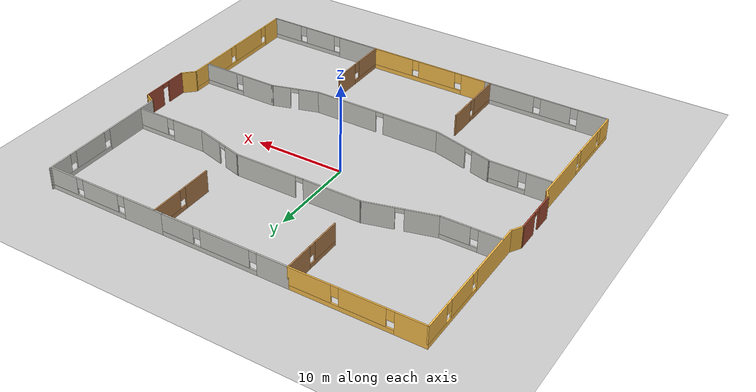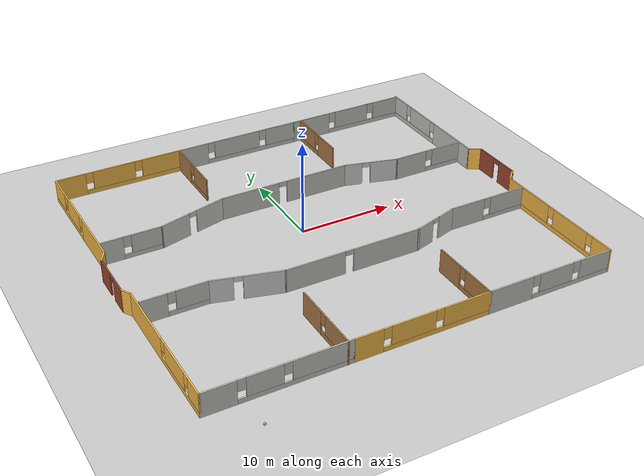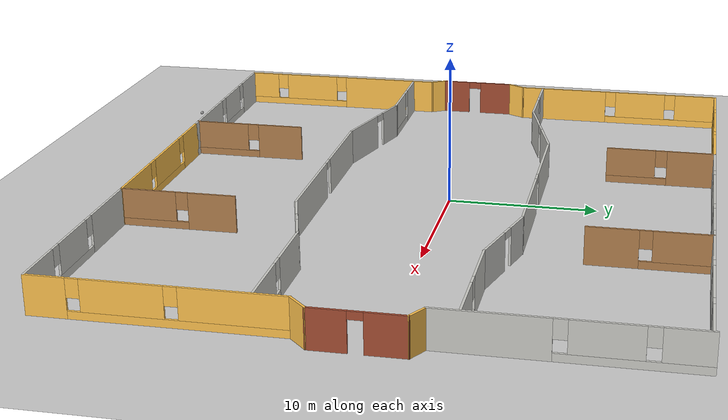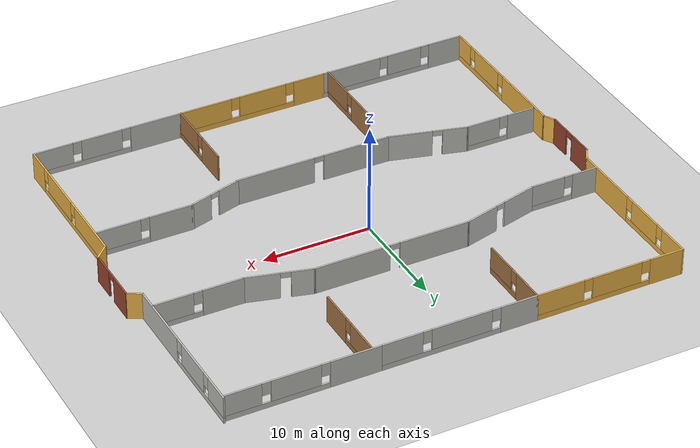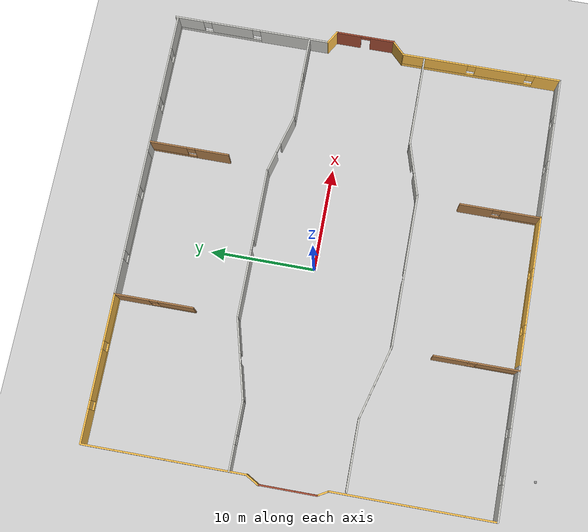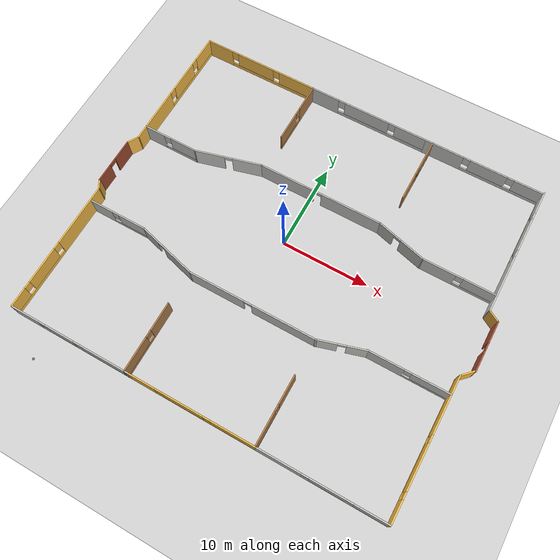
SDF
<sdf version="1.6">
 <world name="default">
  <plugin name="welcome_message" filename="libwelcome_message.so"/>
  <light name="sun" type="directional">
   <pose>0 0 10 0 -0 0</pose>
   <diffuse>0.8 0.8 0.8 1</diffuse>
   <specular>0.2 0.2 0.2 1</specular>
   <attenuation>
    <range>1000</range>
    <constant>0.9</constant>
    <linear>0.01</linear>
    <quadratic>0.001</quadratic>
   </attenuation>
   <direction>-0.5 0.1 -0.9</direction>
  </light>
  <model name="ground_plane">
   <static>1</static>
   <link name="link">
    <collision name="collision">
     <geometry><plane><normal>0 0 1</normal><size>100 100</size></plane></geometry>
     <surface><friction><ode><mu>100</mu><mu2>50</mu2></ode></friction></surface>
    </collision>
    <visual name="visual">
     <cast_shadows>0</cast_shadows>
     <geometry><plane><normal>0 0 1</normal><size>100 100</size></plane></geometry>
     <material>
      <script><uri>file://media/materials/scripts/gazebo.material</uri><name>Gazebo/Grey</name></script>
     </material>
    </visual>
   </link>
  </model>
  <gravity>0 0 -9.8</gravity>
  <magnetic_field>6e-06 2.3e-05 -4.2e-05</magnetic_field>
  <atmosphere type="adiabatic"/>
  <physics name="default_physics" default="0" type="ode">
   <max_step_size>0.001</max_step_size>
   <real_time_factor>1</real_time_factor>
   <real_time_update_rate>1000</real_time_update_rate>
  </physics>
  <scene><ambient>0.4 0.4 0.4 1</ambient><background>0.7 0.7 0.7 1</background><shadows>1</shadows></scene>
  <spherical_coordinates>
   <surface_model>EARTH_WGS84</surface_model>
   <latitude_deg>0</latitude_deg>
   <longitude_deg>0</longitude_deg>
   <elevation>0</elevation>
   <heading_deg>0</heading_deg>
  </spherical_coordinates>
  <model name="model">
   <pose>1.3797 -1.1711 0 0 -0 0</pose>
   <link name="Wall_22">
    <pose>-21.3175 -11.3683 0 0 0 -1.5708</pose>
    <visual name="Wall_22_Visual_0">
     <pose>-3.98783 0 1.25 0 -0 0</pose>
     <geometry><box><size>7.27435 0.15 2.5</size></box></geometry>
     <material>
      <script><uri>file://media/materials/scripts/gazebo.material</uri><name>Gazebo/Grey</name></script>
      <ambient>1 0.764706 0.305882 1</ambient>
     </material>
     <meta><layer>0</layer></meta>
    </visual>
    <collision name="Wall_22_Collision_0">
     <geometry><box><size>7.27435 0.15 2.5</size></box></geometry>
     <pose>-3.98783 0 1.25 0 -0 0</pose>
    </collision>
    <visual name="Wall_22_Visual_1">
     <pose>3.63717 0 0.25 0 -0 0</pose>
     <geometry><box><size>7.97565 0.15 0.5</size></box></geometry>
     <material>
      <script><uri>file://media/materials/scripts/gazebo.material</uri><name>Gazebo/Grey</name></script>
      <ambient>1 0.764706 0.305882 1</ambient>
     </material>
     <meta><layer>0</layer></meta>
    </visual>
    <collision name="Wall_22_Collision_1">
     <geometry><box><size>7.97565 0.15 0.5</size></box></geometry>
     <pose>3.63717 0 0.25 0 -0 0</pose>
    </collision>
    <visual name="Wall_22_Visual_2">
     <pose>2.53115 0 1.5 0 -0 0</pose>
     <geometry><box><size>4.16361 0.15 2</size></box></geometry>
     <material>
      <script><uri>file://media/materials/scripts/gazebo.material</uri><name>Gazebo/Grey</name></script>
      <ambient>1 0.764706 0.305882 1</ambient>
     </material>
     <meta><layer>0</layer></meta>
    </visual>
    <collision name="Wall_22_Collision_2">
     <geometry><box><size>4.16361 0.15 2</size></box></geometry>
     <pose>2.53115 0 1.5 0 -0 0</pose>
    </collision>
    <visual name="Wall_22_Visual_3">
     <pose>6.51898 0 1.5 0 -0 0</pose>
     <geometry><box><size>2.21204 0.15 2</size></box></geometry>
     <material>
      <script><uri>file://media/materials/scripts/gazebo.material</uri><name>Gazebo/Grey</name></script>
      <ambient>1 0.764706 0.305882 1</ambient>
     </material>
     <meta><layer>0</layer></meta>
    </visual>
    <collision name="Wall_22_Collision_3">
     <geometry><box><size>2.21204 0.15 2</size></box></geometry>
     <pose>6.51898 0 1.5 0 -0 0</pose>
    </collision>
    <visual name="Wall_22_Visual_4">
     <pose>0.049349 0 1.9 0 -0 0</pose>
     <geometry><box><size>0.8 0.15 1.2</size></box></geometry>
     <material>
      <script><uri>file://media/materials/scripts/gazebo.material</uri><name>Gazebo/Grey</name></script>
      <ambient>1 0.764706 0.305882 1</ambient>
     </material>
     <meta><layer>0</layer></meta>
    </visual>
    <collision name="Wall_22_Collision_4">
     <geometry><box><size>0.8 0.15 1.2</size></box></geometry>
     <pose>0.049349 0 1.9 0 -0 0</pose>
    </collision>
    <visual name="Wall_22_Visual_5">
     <pose>5.01296 0 1.9 0 -0 0</pose>
     <geometry><box><size>0.8 0.15 1.2</size></box></geometry>
     <material>
      <script><uri>file://media/materials/scripts/gazebo.material</uri><name>Gazebo/Grey</name></script>
      <ambient>1 0.764706 0.305882 1</ambient>
     </material>
     <meta><layer>0</layer></meta>
    </visual>
    <collision name="Wall_22_Collision_5">
     <geometry><box><size>0.8 0.15 1.2</size></box></geometry>
     <pose>5.01296 0 1.9 0 -0 0</pose>
    </collision>
   </link>
   <link name="Wall_23">
    <pose>-14.2675 -18.9183 0 0 -0 0</pose>
    <visual name="Wall_23_Visual_0">
     <pose>-5.44036 0 1.25 0 -0 0</pose>
     <geometry><box><size>3.36928 0.15 2.5</size></box></geometry>
     <material>
      <script><uri>file://media/materials/scripts/gazebo.material</uri><name>Gazebo/CeilingTiled</name></script>
      <ambient>1 0.764706 0.305882 1</ambient>
     </material>
     <meta><layer>0</layer></meta>
    </visual>
    <collision name="Wall_23_Collision_0">
     <geometry><box><size>3.36928 0.15 2.5</size></box></geometry>
     <pose>-5.44036 0 1.25 0 -0 0</pose>
    </collision>
    <visual name="Wall_23_Visual_1">
     <pose>1.68464 0 0.25 0 -0 0</pose>
     <geometry><box><size>10.8807 0.15 0.5</size></box></geometry>
     <material>
      <script><uri>file://media/materials/scripts/gazebo.material</uri><name>Gazebo/CeilingTiled</name></script>
      <ambient>1 0.764706 0.305882 1</ambient>
     </material>
     <meta><layer>0</layer></meta>
    </visual>
    <collision name="Wall_23_Collision_1">
     <geometry><box><size>10.8807 0.15 0.5</size></box></geometry>
     <pose>1.68464 0 0.25 0 -0 0</pose>
    </collision>
    <visual name="Wall_23_Visual_2">
     <pose>-1.24407 0 1.5 0 -0 0</pose>
     <geometry><box><size>3.42331 0.15 2</size></box></geometry>
     <material>
      <script><uri>file://media/materials/scripts/gazebo.material</uri><name>Gazebo/CeilingTiled</name></script>
      <ambient>1 0.764706 0.305882 1</ambient>
     </material>
     <meta><layer>0</layer></meta>
    </visual>
    <collision name="Wall_23_Collision_2">
     <geometry><box><size>3.42331 0.15 2</size></box></geometry>
     <pose>-1.24407 0 1.5 0 -0 0</pose>
    </collision>
    <visual name="Wall_23_Visual_3">
     <pose>4.19629 0 1.5 0 -0 0</pose>
     <geometry><box><size>5.85741 0.15 2</size></box></geometry>
     <material>
      <script><uri>file://media/materials/scripts/gazebo.material</uri><name>Gazebo/CeilingTiled</name></script>
      <ambient>1 0.764706 0.305882 1</ambient>
     </material>
     <meta><layer>0</layer></meta>
    </visual>
    <collision name="Wall_23_Collision_3">
     <geometry><box><size>5.85741 0.15 2</size></box></geometry>
     <pose>4.19629 0 1.5 0 -0 0</pose>
    </collision>
    <visual name="Wall_23_Visual_4">
     <pose>-3.35572 0 1.9 0 -0 0</pose>
     <geometry><box><size>0.8 0.15 1.2</size></box></geometry>
     <material>
      <script><uri>file://media/materials/scripts/gazebo.material</uri><name>Gazebo/CeilingTiled</name></script>
      <ambient>1 0.764706 0.305882 1</ambient>
     </material>
     <meta><layer>0</layer></meta>
    </visual>
    <collision name="Wall_23_Collision_4">
     <geometry><box><size>0.8 0.15 1.2</size></box></geometry>
     <pose>-3.35572 0 1.9 0 -0 0</pose>
    </collision>
    <visual name="Wall_23_Visual_5">
     <pose>0.867585 0 1.9 0 -0 0</pose>
     <geometry><box><size>0.8 0.15 1.2</size></box></geometry>
     <material>
      <script><uri>file://media/materials/scripts/gazebo.material</uri><name>Gazebo/CeilingTiled</name></script>
      <ambient>1 0.764706 0.305882 1</ambient>
     </material>
     <meta><layer>0</layer></meta>
    </visual>
    <collision name="Wall_23_Collision_5">
     <geometry><box><size>0.8 0.15 1.2</size></box></geometry>
     <pose>0.867585 0 1.9 0 -0 0</pose>
    </collision>
   </link>
   <link name="Wall_24">
    <pose>-0.167493 -18.9183 0 0 -0 0</pose>
    <visual name="Wall_24_Visual_0">
     <pose>-5.61853 0 1.25 0 -0 0</pose>
     <geometry><box><size>3.01295 0.15 2.5</size></box></geometry>
     <material>
      <script><uri>file://media/materials/scripts/gazebo.material</uri><name>Gazebo/Grey</name></script>
      <ambient>1 0.764706 0.305882 1</ambient>
     </material>
     <meta><layer>0</layer></meta>
    </visual>
    <collision name="Wall_24_Collision_0">
     <geometry><box><size>3.01295 0.15 2.5</size></box></geometry>
     <pose>-5.61853 0 1.25 0 -0 0</pose>
    </collision>
    <visual name="Wall_24_Visual_1">
     <pose>1.50647 0 0.25 0 -0 0</pose>
     <geometry><box><size>11.2371 0.15 0.5</size></box></geometry>
     <material>
      <script><uri>file://media/materials/scripts/gazebo.material</uri><name>Gazebo/Grey</name></script>
      <ambient>1 0.764706 0.305882 1</ambient>
     </material>
     <meta><layer>0</layer></meta>
    </visual>
    <collision name="Wall_24_Collision_1">
     <geometry><box><size>11.2371 0.15 0.5</size></box></geometry>
     <pose>1.50647 0 0.25 0 -0 0</pose>
    </collision>
    <visual name="Wall_24_Visual_2">
     <pose>-1.02682 0 1.5 0 -0 0</pose>
     <geometry><box><size>4.57046 0.15 2</size></box></geometry>
     <material>
      <script><uri>file://media/materials/scripts/gazebo.material</uri><name>Gazebo/Grey</name></script>
      <ambient>1 0.764706 0.305882 1</ambient>
     </material>
     <meta><layer>0</layer></meta>
    </visual>
    <collision name="Wall_24_Collision_2">
     <geometry><box><size>4.57046 0.15 2</size></box></geometry>
     <pose>-1.02682 0 1.5 0 -0 0</pose>
    </collision>
    <visual name="Wall_24_Visual_3">
     <pose>4.5917 0 1.5 0 -0 0</pose>
     <geometry><box><size>5.06659 0.15 2</size></box></geometry>
     <material>
      <script><uri>file://media/materials/scripts/gazebo.material</uri><name>Gazebo/Grey</name></script>
      <ambient>1 0.764706 0.305882 1</ambient>
     </material>
     <meta><layer>0</layer></meta>
    </visual>
    <collision name="Wall_24_Collision_3">
     <geometry><box><size>5.06659 0.15 2</size></box></geometry>
     <pose>4.5917 0 1.5 0 -0 0</pose>
    </collision>
    <visual name="Wall_24_Visual_4">
     <pose>-3.71205 0 1.9 0 -0 0</pose>
     <geometry><box><size>0.8 0.15 1.2</size></box></geometry>
     <material>
      <script><uri>file://media/materials/scripts/gazebo.material</uri><name>Gazebo/Grey</name></script>
      <ambient>1 0.764706 0.305882 1</ambient>
     </material>
     <meta><layer>0</layer></meta>
    </visual>
    <collision name="Wall_24_Collision_4">
     <geometry><box><size>0.8 0.15 1.2</size></box></geometry>
     <pose>-3.71205 0 1.9 0 -0 0</pose>
    </collision>
    <visual name="Wall_24_Visual_5">
     <pose>1.65841 0 1.9 0 -0 0</pose>
     <geometry><box><size>0.8 0.15 1.2</size></box></geometry>
     <material>
      <script><uri>file://media/materials/scripts/gazebo.material</uri><name>Gazebo/Grey</name></script>
      <ambient>1 0.764706 0.305882 1</ambient>
     </material>
     <meta><layer>0</layer></meta>
    </visual>
    <collision name="Wall_24_Collision_5">
     <geometry><box><size>0.8 0.15 1.2</size></box></geometry>
     <pose>1.65841 0 1.9 0 -0 0</pose>
    </collision>
   </link>
   <link name="Wall_25">
    <pose>13.8075 -18.9183 0 0 -0 0</pose>
    <visual name="Wall_25_Visual_0">
     <pose>-4.56921 0 1.25 0 -0 0</pose>
     <geometry><box><size>4.86159 0.15 2.5</size></box></geometry>
     <material>
      <script><uri>file://media/materials/scripts/gazebo.material</uri><name>Gazebo/CeilingTiled</name></script>
      <ambient>1 0.764706 0.305882 1</ambient>
     </material>
     <meta><layer>0</layer></meta>
    </visual>
    <collision name="Wall_25_Collision_0">
     <geometry><box><size>4.86159 0.15 2.5</size></box></geometry>
     <pose>-4.56921 0 1.25 0 -0 0</pose>
    </collision>
    <visual name="Wall_25_Visual_1">
     <pose>2.43079 0 0.25 0 -0 0</pose>
     <geometry><box><size>9.13841 0.15 0.5</size></box></geometry>
     <material>
      <script><uri>file://media/materials/scripts/gazebo.material</uri><name>Gazebo/CeilingTiled</name></script>
      <ambient>1 0.764706 0.305882 1</ambient>
     </material>
     <meta><layer>0</layer></meta>
    </visual>
    <collision name="Wall_25_Collision_1">
     <geometry><box><size>9.13841 0.15 0.5</size></box></geometry>
     <pose>2.43079 0 0.25 0 -0 0</pose>
    </collision>
    <visual name="Wall_25_Visual_2">
     <pose>0.58065 0 1.5 0 -0 0</pose>
     <geometry><box><size>3.83812 0.15 2</size></box></geometry>
     <material>
      <script><uri>file://media/materials/scripts/gazebo.material</uri><name>Gazebo/CeilingTiled</name></script>
      <ambient>1 0.764706 0.305882 1</ambient>
     </material>
     <meta><layer>0</layer></meta>
    </visual>
    <collision name="Wall_25_Collision_2">
     <geometry><box><size>3.83812 0.15 2</size></box></geometry>
     <pose>0.58065 0 1.5 0 -0 0</pose>
    </collision>
    <visual name="Wall_25_Visual_3">
     <pose>5.14986 0 1.5 0 -0 0</pose>
     <geometry><box><size>3.70029 0.15 2</size></box></geometry>
     <material>
      <script><uri>file://media/materials/scripts/gazebo.material</uri><name>Gazebo/CeilingTiled</name></script>
      <ambient>1 0.764706 0.305882 1</ambient>
     </material>
     <meta><layer>0</layer></meta>
    </visual>
    <collision name="Wall_25_Collision_3">
     <geometry><box><size>3.70029 0.15 2</size></box></geometry>
     <pose>5.14986 0 1.5 0 -0 0</pose>
    </collision>
    <visual name="Wall_25_Visual_4">
     <pose>-1.73841 0 1.9 0 -0 0</pose>
     <geometry><box><size>0.8 0.15 1.2</size></box></geometry>
     <material>
      <script><uri>file://media/materials/scripts/gazebo.material</uri><name>Gazebo/CeilingTiled</name></script>
      <ambient>1 0.764706 0.305882 1</ambient>
     </material>
     <meta><layer>0</layer></meta>
    </visual>
    <collision name="Wall_25_Collision_4">
     <geometry><box><size>0.8 0.15 1.2</size></box></geometry>
     <pose>-1.73841 0 1.9 0 -0 0</pose>
    </collision>
    <visual name="Wall_25_Visual_5">
     <pose>2.89971 0 1.9 0 -0 0</pose>
     <geometry><box><size>0.8 0.15 1.2</size></box></geometry>
     <material>
      <script><uri>file://media/materials/scripts/gazebo.material</uri><name>Gazebo/CeilingTiled</name></script>
      <ambient>1 0.764706 0.305882 1</ambient>
     </material>
     <meta><layer>0</layer></meta>
    </visual>
    <collision name="Wall_25_Collision_5">
     <geometry><box><size>0.8 0.15 1.2</size></box></geometry>
     <pose>2.89971 0 1.9 0 -0 0</pose>
    </collision>
   </link>
   <link name="Wall_26">
    <pose>20.7325 -11.2433 0 0 -0 1.5708</pose>
    <visual name="Wall_26_Visual_0">
     <pose>-6.48124 0 1.25 0 -0 0</pose>
     <geometry><box><size>2.53753 0.15 2.5</size></box></geometry>
     <material>
      <script><uri>file://media/materials/scripts/gazebo.material</uri><name>Gazebo/Grey</name></script>
      <ambient>1 0.764706 0.305882 1</ambient>
     </material>
     <meta><layer>0</layer></meta>
    </visual>
    <collision name="Wall_26_Collision_0">
     <geometry><box><size>2.53753 0.15 2.5</size></box></geometry>
     <pose>-6.48124 0 1.25 0 -0 0</pose>
    </collision>
    <visual name="Wall_26_Visual_1">
     <pose>1.26876 0 0.25 0 -0 0</pose>
     <geometry><box><size>12.9625 0.15 0.5</size></box></geometry>
     <material>
      <script><uri>file://media/materials/scripts/gazebo.material</uri><name>Gazebo/Grey</name></script>
      <ambient>1 0.764706 0.305882 1</ambient>
     </material>
     <meta><layer>0</layer></meta>
    </visual>
    <collision name="Wall_26_Collision_1">
     <geometry><box><size>12.9625 0.15 0.5</size></box></geometry>
     <pose>1.26876 0 0.25 0 -0 0</pose>
    </collision>
    <visual name="Wall_26_Visual_2">
     <pose>-1.95201 0 1.5 0 -0 0</pose>
     <geometry><box><size>4.92092 0.15 2</size></box></geometry>
     <material>
      <script><uri>file://media/materials/scripts/gazebo.material</uri><name>Gazebo/Grey</name></script>
      <ambient>1 0.764706 0.305882 1</ambient>
     </material>
     <meta><layer>0</layer></meta>
    </visual>
    <collision name="Wall_26_Collision_2">
     <geometry><box><size>4.92092 0.15 2</size></box></geometry>
     <pose>-1.95201 0 1.5 0 -0 0</pose>
    </collision>
    <visual name="Wall_26_Visual_3">
     <pose>4.52922 0 1.5 0 -0 0</pose>
     <geometry><box><size>6.44155 0.15 2</size></box></geometry>
     <material>
      <script><uri>file://media/materials/scripts/gazebo.material</uri><name>Gazebo/Grey</name></script>
      <ambient>1 0.764706 0.305882 1</ambient>
     </material>
     <meta><layer>0</layer></meta>
    </visual>
    <collision name="Wall_26_Collision_3">
     <geometry><box><size>6.44155 0.15 2</size></box></geometry>
     <pose>4.52922 0 1.5 0 -0 0</pose>
    </collision>
    <visual name="Wall_26_Visual_4">
     <pose>-4.81247 0 1.9 0 -0 0</pose>
     <geometry><box><size>0.8 0.15 1.2</size></box></geometry>
     <material>
      <script><uri>file://media/materials/scripts/gazebo.material</uri><name>Gazebo/Grey</name></script>
      <ambient>1 0.764706 0.305882 1</ambient>
     </material>
     <meta><layer>0</layer></meta>
    </visual>
    <collision name="Wall_26_Collision_4">
     <geometry><box><size>0.8 0.15 1.2</size></box></geometry>
     <pose>-4.81247 0 1.9 0 -0 0</pose>
    </collision>
    <visual name="Wall_26_Visual_5">
     <pose>0.908446 0 1.9 0 -0 0</pose>
     <geometry><box><size>0.8 0.15 1.2</size></box></geometry>
     <material>
      <script><uri>file://media/materials/scripts/gazebo.material</uri><name>Gazebo/Grey</name></script>
      <ambient>1 0.764706 0.305882 1</ambient>
     </material>
     <meta><layer>0</layer></meta>
    </visual>
    <collision name="Wall_26_Collision_5">
     <geometry><box><size>0.8 0.15 1.2</size></box></geometry>
     <pose>0.908446 0 1.9 0 -0 0</pose>
    </collision>
   </link>
   <link name="Wall_27">
    <collision name="Wall_27_Collision">
     <geometry><box><size>1.75 0.15 2.5</size></box></geometry>
     <pose>0 0 1.25 0 -0 0</pose>
    </collision>
    <visual name="Wall_27_Visual">
     <pose>0 0 1.25 0 -0 0</pose>
     <geometry><box><size>1.75 0.15 2.5</size></box></geometry>
     <material>
      <script><uri>file://media/materials/scripts/gazebo.material</uri><name>Gazebo/Grey</name></script>
      <ambient>1 0.764706 0.305882 1</ambient>
     </material>
     <meta><layer>0</layer></meta>
    </visual>
    <pose>21.2982 -3.00259 0 0 -0 0.785398</pose>
   </link>
   <link name="Wall_28">
    <pose>21.8639 0.363092 0 0 -0 1.5708</pose>
    <visual name="Wall_28_Visual_0">
     <pose>-1.69424 0 1.25 0 -0 0</pose>
     <geometry><box><size>2.36151 0.15 2.5</size></box></geometry>
     <material>
      <script><uri>file://media/materials/scripts/gazebo.material</uri><name>Gazebo/Bricks</name></script>
      <ambient>1 1 1 1</ambient>
     </material>
     <meta><layer>0</layer></meta>
    </visual>
    <collision name="Wall_28_Collision_0">
     <geometry><box><size>2.36151 0.15 2.5</size></box></geometry>
     <pose>-1.69424 0 1.25 0 -0 0</pose>
    </collision>
    <visual name="Wall_28_Visual_1">
     <pose>1.63076 0 1.25 0 -0 0</pose>
     <geometry><box><size>2.48849 0.15 2.5</size></box></geometry>
     <material>
      <script><uri>file://media/materials/scripts/gazebo.material</uri><name>Gazebo/Bricks</name></script>
      <ambient>1 1 1 1</ambient>
     </material>
     <meta><layer>0</layer></meta>
    </visual>
    <collision name="Wall_28_Collision_1">
     <geometry><box><size>2.48849 0.15 2.5</size></box></geometry>
     <pose>1.63076 0 1.25 0 -0 0</pose>
    </collision>
    <visual name="Wall_28_Visual_2">
     <pose>-0.063486 0 2.25 0 -0 0</pose>
     <geometry><box><size>0.9 0.15 0.5</size></box></geometry>
     <material>
      <script><uri>file://media/materials/scripts/gazebo.material</uri><name>Gazebo/Bricks</name></script>
      <ambient>1 1 1 1</ambient>
     </material>
     <meta><layer>0</layer></meta>
    </visual>
    <collision name="Wall_28_Collision_2">
     <geometry><box><size>0.9 0.15 0.5</size></box></geometry>
     <pose>-0.063486 0 2.25 0 -0 0</pose>
    </collision>
   </link>
   <link name="Wall_29">
    <collision name="Wall_29_Collision">
     <geometry><box><size>1.5 0.15 2.5</size></box></geometry>
     <pose>0 0 1.25 0 -0 0</pose>
    </collision>
    <visual name="Wall_29_Visual">
     <pose>0 0 1.25 0 -0 0</pose>
     <geometry><box><size>1.5 0.15 2.5</size></box></geometry>
     <material>
      <script><uri>file://media/materials/scripts/gazebo.material</uri><name>Gazebo/Grey</name></script>
      <ambient>1 0.764706 0.305882 1</ambient>
     </material>
     <meta><layer>0</layer></meta>
    </visual>
    <pose>21.2793 3.50059 0 0 -0 2.61799</pose>
   </link>
   <link name="Wall_36">
    <collision name="Wall_36_Collision">
     <geometry><box><size>1.25 0.15 2.5</size></box></geometry>
     <pose>0 0 1.25 0 -0 0</pose>
    </collision>
    <visual name="Wall_36_Visual">
     <pose>0 0 1.25 0 -0 0</pose>
     <geometry><box><size>1.25 0.15 2.5</size></box></geometry>
     <material>
      <script><uri>file://media/materials/scripts/gazebo.material</uri><name>Gazebo/Grey</name></script>
      <ambient>1 0.764706 0.305882 1</ambient>
     </material>
     <meta><layer>0</layer></meta>
    </visual>
    <pose>-21.5925 -3.34197 0 0 -0 2.0944</pose>
   </link>
   <link name="Wall_37">
    <pose>-21.8675 -0.190651 0 0 -0 1.5708</pose>
    <visual name="Wall_37_Visual_0">
     <pose>-1.69498 0 1.25 0 -0 0</pose>
     <geometry><box><size>2.11003 0.15 2.5</size></box></geometry>
     <material>
      <script><uri>file://media/materials/scripts/gazebo.material</uri><name>Gazebo/Bricks</name></script>
      <ambient>1 1 1 1</ambient>
     </material>
     <meta><layer>0</layer></meta>
    </visual>
    <collision name="Wall_37_Collision_0">
     <geometry><box><size>2.11003 0.15 2.5</size></box></geometry>
     <pose>-1.69498 0 1.25 0 -0 0</pose>
    </collision>
    <visual name="Wall_37_Visual_1">
     <pose>1.50502 0 1.25 0 -0 0</pose>
     <geometry><box><size>2.48997 0.15 2.5</size></box></geometry>
     <material>
      <script><uri>file://media/materials/scripts/gazebo.material</uri><name>Gazebo/Bricks</name></script>
      <ambient>1 1 1 1</ambient>
     </material>
     <meta><layer>0</layer></meta>
    </visual>
    <collision name="Wall_37_Collision_1">
     <geometry><box><size>2.48997 0.15 2.5</size></box></geometry>
     <pose>1.50502 0 1.25 0 -0 0</pose>
    </collision>
    <visual name="Wall_37_Visual_2">
     <pose>-0.189968 0 2.25 0 -0 0</pose>
     <geometry><box><size>0.9 0.15 0.5</size></box></geometry>
     <material>
      <script><uri>file://media/materials/scripts/gazebo.material</uri><name>Gazebo/Bricks</name></script>
      <ambient>1 1 1 1</ambient>
     </material>
     <meta><layer>0</layer></meta>
    </visual>
    <collision name="Wall_37_Collision_2">
     <geometry><box><size>0.9 0.15 0.5</size></box></geometry>
     <pose>-0.189968 0 2.25 0 -0 0</pose>
    </collision>
   </link>
   <link name="Wall_38">
    <collision name="Wall_38_Collision">
     <geometry><box><size>1.5 0.15 2.5</size></box></geometry>
     <pose>0 0 1.25 0 -0 0</pose>
    </collision>
    <visual name="Wall_38_Visual">
     <pose>0 0 1.25 0 -0 0</pose>
     <geometry><box><size>1.5 0.15 2.5</size></box></geometry>
     <material>
      <script><uri>file://media/materials/scripts/gazebo.material</uri><name>Gazebo/Grey</name></script>
      <ambient>1 0.764706 0.305882 1</ambient>
     </material>
     <meta><layer>0</layer></meta>
    </visual>
    <pose>-21.53 3.06892 0 0 -0 1.0472</pose>
   </link>
   <link name="Wall_40">
    <pose>-21.1925 11.2035 0 0 -0 1.5708</pose>
    <visual name="Wall_40_Visual_0">
     <pose>-4.29734 0 1.25 0 -0 0</pose>
     <geometry><box><size>6.65533 0.15 2.5</size></box></geometry>
     <material>
      <script><uri>file://media/materials/scripts/gazebo.material</uri><name>Gazebo/Grey</name></script>
      <ambient>1 0.764706 0.305882 1</ambient>
     </material>
     <meta><layer>0</layer></meta>
    </visual>
    <collision name="Wall_40_Collision_0">
     <geometry><box><size>6.65533 0.15 2.5</size></box></geometry>
     <pose>-4.29734 0 1.25 0 -0 0</pose>
    </collision>
    <visual name="Wall_40_Visual_1">
     <pose>3.32766 0 0.25 0 -0 0</pose>
     <geometry><box><size>8.59467 0.15 0.5</size></box></geometry>
     <material>
      <script><uri>file://media/materials/scripts/gazebo.material</uri><name>Gazebo/Grey</name></script>
      <ambient>1 0.764706 0.305882 1</ambient>
     </material>
     <meta><layer>0</layer></meta>
    </visual>
    <collision name="Wall_40_Collision_1">
     <geometry><box><size>8.59467 0.15 0.5</size></box></geometry>
     <pose>3.32766 0 0.25 0 -0 0</pose>
    </collision>
    <visual name="Wall_40_Visual_2">
     <pose>1.74939 0 1.5 0 -0 0</pose>
     <geometry><box><size>3.83812 0.15 2</size></box></geometry>
     <material>
      <script><uri>file://media/materials/scripts/gazebo.material</uri><name>Gazebo/Grey</name></script>
      <ambient>1 0.764706 0.305882 1</ambient>
     </material>
     <meta><layer>0</layer></meta>
    </visual>
    <collision name="Wall_40_Collision_2">
     <geometry><box><size>3.83812 0.15 2</size></box></geometry>
     <pose>1.74939 0 1.5 0 -0 0</pose>
    </collision>
    <visual name="Wall_40_Visual_3">
     <pose>6.04673 0 1.5 0 -0 0</pose>
     <geometry><box><size>3.15655 0.15 2</size></box></geometry>
     <material>
      <script><uri>file://media/materials/scripts/gazebo.material</uri><name>Gazebo/Grey</name></script>
      <ambient>1 0.764706 0.305882 1</ambient>
     </material>
     <meta><layer>0</layer></meta>
    </visual>
    <collision name="Wall_40_Collision_3">
     <geometry><box><size>3.15655 0.15 2</size></box></geometry>
     <pose>6.04673 0 1.5 0 -0 0</pose>
    </collision>
    <visual name="Wall_40_Visual_4">
     <pose>-0.569674 0 1.9 0 -0 0</pose>
     <geometry><box><size>0.8 0.15 1.2</size></box></geometry>
     <material>
      <script><uri>file://media/materials/scripts/gazebo.material</uri><name>Gazebo/Grey</name></script>
      <ambient>1 0.764706 0.305882 1</ambient>
     </material>
     <meta><layer>0</layer></meta>
    </visual>
    <collision name="Wall_40_Collision_4">
     <geometry><box><size>0.8 0.15 1.2</size></box></geometry>
     <pose>-0.569674 0 1.9 0 -0 0</pose>
    </collision>
    <visual name="Wall_40_Visual_5">
     <pose>4.06845 0 1.9 0 -0 0</pose>
     <geometry><box><size>0.8 0.15 1.2</size></box></geometry>
     <material>
      <script><uri>file://media/materials/scripts/gazebo.material</uri><name>Gazebo/Grey</name></script>
      <ambient>1 0.764706 0.305882 1</ambient>
     </material>
     <meta><layer>0</layer></meta>
    </visual>
    <collision name="Wall_40_Collision_5">
     <geometry><box><size>0.8 0.15 1.2</size></box></geometry>
     <pose>4.06845 0 1.9 0 -0 0</pose>
    </collision>
   </link>
   <link name="Wall_42">
    <pose>20.6947 11.3881 0 0 -0 1.5708</pose>
    <visual name="Wall_42_Visual_0">
     <pose>-4.22815 0 1.25 0 -0 0</pose>
     <geometry><box><size>6.7937 0.15 2.5</size></box></geometry>
     <material>
      <script><uri>file://media/materials/scripts/gazebo.material</uri><name>Gazebo/CeilingTiled</name></script>
      <ambient>1 0.764706 0.305882 1</ambient>
     </material>
     <meta><layer>0</layer></meta>
    </visual>
    <collision name="Wall_42_Collision_0">
     <geometry><box><size>6.7937 0.15 2.5</size></box></geometry>
     <pose>-4.22815 0 1.25 0 -0 0</pose>
    </collision>
    <visual name="Wall_42_Visual_1">
     <pose>3.39685 0 0.25 0 -0 0</pose>
     <geometry><box><size>8.4563 0.15 0.5</size></box></geometry>
     <material>
      <script><uri>file://media/materials/scripts/gazebo.material</uri><name>Gazebo/CeilingTiled</name></script>
      <ambient>1 0.764706 0.305882 1</ambient>
     </material>
     <meta><layer>0</layer></meta>
    </visual>
    <collision name="Wall_42_Collision_1">
     <geometry><box><size>8.4563 0.15 0.5</size></box></geometry>
     <pose>3.39685 0 0.25 0 -0 0</pose>
    </collision>
    <visual name="Wall_42_Visual_2">
     <pose>2.00082 0 1.5 0 -0 0</pose>
     <geometry><box><size>4.06425 0.15 2</size></box></geometry>
     <material>
      <script><uri>file://media/materials/scripts/gazebo.material</uri><name>Gazebo/CeilingTiled</name></script>
      <ambient>1 0.764706 0.305882 1</ambient>
     </material>
     <meta><layer>0</layer></meta>
    </visual>
    <collision name="Wall_42_Collision_2">
     <geometry><box><size>4.06425 0.15 2</size></box></geometry>
     <pose>2.00082 0 1.5 0 -0 0</pose>
    </collision>
    <visual name="Wall_42_Visual_3">
     <pose>6.22897 0 1.5 0 -0 0</pose>
     <geometry><box><size>2.79205 0.15 2</size></box></geometry>
     <material>
      <script><uri>file://media/materials/scripts/gazebo.material</uri><name>Gazebo/CeilingTiled</name></script>
      <ambient>1 0.764706 0.305882 1</ambient>
     </material>
     <meta><layer>0</layer></meta>
    </visual>
    <collision name="Wall_42_Collision_3">
     <geometry><box><size>2.79205 0.15 2</size></box></geometry>
     <pose>6.22897 0 1.5 0 -0 0</pose>
    </collision>
    <visual name="Wall_42_Visual_4">
     <pose>-0.431303 0 1.9 0 -0 0</pose>
     <geometry><box><size>0.8 0.15 1.2</size></box></geometry>
     <material>
      <script><uri>file://media/materials/scripts/gazebo.material</uri><name>Gazebo/CeilingTiled</name></script>
      <ambient>1 0.764706 0.305882 1</ambient>
     </material>
     <meta><layer>0</layer></meta>
    </visual>
    <collision name="Wall_42_Collision_4">
     <geometry><box><size>0.8 0.15 1.2</size></box></geometry>
     <pose>-0.431303 0 1.9 0 -0 0</pose>
    </collision>
    <visual name="Wall_42_Visual_5">
     <pose>4.43295 0 1.9 0 -0 0</pose>
     <geometry><box><size>0.8 0.15 1.2</size></box></geometry>
     <material>
      <script><uri>file://media/materials/scripts/gazebo.material</uri><name>Gazebo/CeilingTiled</name></script>
      <ambient>1 0.764706 0.305882 1</ambient>
     </material>
     <meta><layer>0</layer></meta>
    </visual>
    <collision name="Wall_42_Collision_5">
     <geometry><box><size>0.8 0.15 1.2</size></box></geometry>
     <pose>4.43295 0 1.9 0 -0 0</pose>
    </collision>
   </link>
   <link name="Wall_51">
    <pose>-14.2675 18.7535 0 0 -0 0</pose>
    <visual name="Wall_51_Visual_0">
     <pose>-5.3786 0 1.25 0 -0 0</pose>
     <geometry><box><size>3.2428 0.15 2.5</size></box></geometry>
     <material>
      <script><uri>file://media/materials/scripts/gazebo.material</uri><name>Gazebo/Grey</name></script>
      <ambient>1 0.764706 0.305882 1</ambient>
     </material>
     <meta><layer>0</layer></meta>
    </visual>
    <collision name="Wall_51_Collision_0">
     <geometry><box><size>3.2428 0.15 2.5</size></box></geometry>
     <pose>-5.3786 0 1.25 0 -0 0</pose>
    </collision>
    <visual name="Wall_51_Visual_1">
     <pose>1.6214 0 0.25 0 -0 0</pose>
     <geometry><box><size>10.7572 0.15 0.5</size></box></geometry>
     <material>
      <script><uri>file://media/materials/scripts/gazebo.material</uri><name>Gazebo/Grey</name></script>
      <ambient>1 0.764706 0.305882 1</ambient>
     </material>
     <meta><layer>0</layer></meta>
    </visual>
    <collision name="Wall_51_Collision_1">
     <geometry><box><size>10.7572 0.15 0.5</size></box></geometry>
     <pose>1.6214 0 0.25 0 -0 0</pose>
    </collision>
    <visual name="Wall_51_Visual_2">
     <pose>-0.618681 0 1.5 0 -0 0</pose>
     <geometry><box><size>4.67704 0.15 2</size></box></geometry>
     <material>
      <script><uri>file://media/materials/scripts/gazebo.material</uri><name>Gazebo/Grey</name></script>
      <ambient>1 0.764706 0.305882 1</ambient>
     </material>
     <meta><layer>0</layer></meta>
    </visual>
    <collision name="Wall_51_Collision_2">
     <geometry><box><size>4.67704 0.15 2</size></box></geometry>
     <pose>-0.618681 0 1.5 0 -0 0</pose>
    </collision>
    <visual name="Wall_51_Visual_3">
     <pose>4.75992 0 1.5 0 -0 0</pose>
     <geometry><box><size>4.48016 0.15 2</size></box></geometry>
     <material>
      <script><uri>file://media/materials/scripts/gazebo.material</uri><name>Gazebo/Grey</name></script>
      <ambient>1 0.764706 0.305882 1</ambient>
     </material>
     <meta><layer>0</layer></meta>
    </visual>
    <collision name="Wall_51_Collision_3">
     <geometry><box><size>4.48016 0.15 2</size></box></geometry>
     <pose>4.75992 0 1.5 0 -0 0</pose>
    </collision>
    <visual name="Wall_51_Visual_4">
     <pose>-3.3572 0 1.9 0 -0 0</pose>
     <geometry><box><size>0.8 0.15 1.2</size></box></geometry>
     <material>
      <script><uri>file://media/materials/scripts/gazebo.material</uri><name>Gazebo/Grey</name></script>
      <ambient>1 0.764706 0.305882 1</ambient>
     </material>
     <meta><layer>0</layer></meta>
    </visual>
    <collision name="Wall_51_Collision_4">
     <geometry><box><size>0.8 0.15 1.2</size></box></geometry>
     <pose>-3.3572 0 1.9 0 -0 0</pose>
    </collision>
    <visual name="Wall_51_Visual_5">
     <pose>2.11984 0 1.9 0 -0 0</pose>
     <geometry><box><size>0.8 0.15 1.2</size></box></geometry>
     <material>
      <script><uri>file://media/materials/scripts/gazebo.material</uri><name>Gazebo/Grey</name></script>
      <ambient>1 0.764706 0.305882 1</ambient>
     </material>
     <meta><layer>0</layer></meta>
    </visual>
    <collision name="Wall_51_Collision_5">
     <geometry><box><size>0.8 0.15 1.2</size></box></geometry>
     <pose>2.11984 0 1.9 0 -0 0</pose>
    </collision>
   </link>
   <link name="Wall_52">
    <pose>-0.292493 18.7535 0 0 -0 0</pose>
    <visual name="Wall_52_Visual_0">
     <pose>-5.39608 0 1.25 0 -0 0</pose>
     <geometry><box><size>3.45785 0.15 2.5</size></box></geometry>
     <material>
      <script><uri>file://media/materials/scripts/gazebo.material</uri><name>Gazebo/CeilingTiled</name></script>
      <ambient>1 0.764706 0.305882 1</ambient>
     </material>
     <meta><layer>0</layer></meta>
    </visual>
    <collision name="Wall_52_Collision_0">
     <geometry><box><size>3.45785 0.15 2.5</size></box></geometry>
     <pose>-5.39608 0 1.25 0 -0 0</pose>
    </collision>
    <visual name="Wall_52_Visual_1">
     <pose>1.72892 0 0.25 0 -0 0</pose>
     <geometry><box><size>10.7922 0.15 0.5</size></box></geometry>
     <material>
      <script><uri>file://media/materials/scripts/gazebo.material</uri><name>Gazebo/CeilingTiled</name></script>
      <ambient>1 0.764706 0.305882 1</ambient>
     </material>
     <meta><layer>0</layer></meta>
    </visual>
    <collision name="Wall_52_Collision_1">
     <geometry><box><size>10.7922 0.15 0.5</size></box></geometry>
     <pose>1.72892 0 0.25 0 -0 0</pose>
    </collision>
    <visual name="Wall_52_Visual_2">
     <pose>-0.115746 0 1.5 0 -0 0</pose>
     <geometry><box><size>5.50281 0.15 2</size></box></geometry>
     <material>
      <script><uri>file://media/materials/scripts/gazebo.material</uri><name>Gazebo/CeilingTiled</name></script>
      <ambient>1 0.764706 0.305882 1</ambient>
     </material>
     <meta><layer>0</layer></meta>
    </visual>
    <collision name="Wall_52_Collision_2">
     <geometry><box><size>5.50281 0.15 2</size></box></geometry>
     <pose>-0.115746 0 1.5 0 -0 0</pose>
    </collision>
    <visual name="Wall_52_Visual_3">
     <pose>5.28033 0 1.5 0 -0 0</pose>
     <geometry><box><size>3.68934 0.15 2</size></box></geometry>
     <material>
      <script><uri>file://media/materials/scripts/gazebo.material</uri><name>Gazebo/CeilingTiled</name></script>
      <ambient>1 0.764706 0.305882 1</ambient>
     </material>
     <meta><layer>0</layer></meta>
    </visual>
    <collision name="Wall_52_Collision_3">
     <geometry><box><size>3.68934 0.15 2</size></box></geometry>
     <pose>5.28033 0 1.5 0 -0 0</pose>
    </collision>
    <visual name="Wall_52_Visual_4">
     <pose>-3.26715 0 1.9 0 -0 0</pose>
     <geometry><box><size>0.8 0.15 1.2</size></box></geometry>
     <material>
      <script><uri>file://media/materials/scripts/gazebo.material</uri><name>Gazebo/CeilingTiled</name></script>
      <ambient>1 0.764706 0.305882 1</ambient>
     </material>
     <meta><layer>0</layer></meta>
    </visual>
    <collision name="Wall_52_Collision_4">
     <geometry><box><size>0.8 0.15 1.2</size></box></geometry>
     <pose>-3.26715 0 1.9 0 -0 0</pose>
    </collision>
    <visual name="Wall_52_Visual_5">
     <pose>3.03566 0 1.9 0 -0 0</pose>
     <geometry><box><size>0.8 0.15 1.2</size></box></geometry>
     <material>
      <script><uri>file://media/materials/scripts/gazebo.material</uri><name>Gazebo/CeilingTiled</name></script>
      <ambient>1 0.764706 0.305882 1</ambient>
     </material>
     <meta><layer>0</layer></meta>
    </visual>
    <collision name="Wall_52_Collision_5">
     <geometry><box><size>0.8 0.15 1.2</size></box></geometry>
     <pose>3.03566 0 1.9 0 -0 0</pose>
    </collision>
   </link>
   <link name="Wall_53">
    <pose>13.6825 18.7535 0 0 -0 0</pose>
    <visual name="Wall_53_Visual_0">
     <pose>-4.64128 0 1.25 0 -0 0</pose>
     <geometry><box><size>4.71744 0.15 2.5</size></box></geometry>
     <material>
      <script><uri>file://media/materials/scripts/gazebo.material</uri><name>Gazebo/CeilingTiled</name></script>
      <ambient>1 0.764706 0.305882 1</ambient>
     </material>
     <meta><layer>0</layer></meta>
    </visual>
    <collision name="Wall_53_Collision_0">
     <geometry><box><size>4.71744 0.15 2.5</size></box></geometry>
     <pose>-4.64128 0 1.25 0 -0 0</pose>
    </collision>
    <visual name="Wall_53_Visual_1">
     <pose>2.35872 0 0.25 0 -0 0</pose>
     <geometry><box><size>9.28256 0.15 0.5</size></box></geometry>
     <material>
      <script><uri>file://media/materials/scripts/gazebo.material</uri><name>Gazebo/CeilingTiled</name></script>
      <ambient>1 0.764706 0.305882 1</ambient>
     </material>
     <meta><layer>0</layer></meta>
    </visual>
    <collision name="Wall_53_Collision_1">
     <geometry><box><size>9.28256 0.15 0.5</size></box></geometry>
     <pose>2.35872 0 0.25 0 -0 0</pose>
    </collision>
    <visual name="Wall_53_Visual_2">
     <pose>0.700074 0 1.5 0 -0 0</pose>
     <geometry><box><size>4.36526 0.15 2</size></box></geometry>
     <material>
      <script><uri>file://media/materials/scripts/gazebo.material</uri><name>Gazebo/CeilingTiled</name></script>
      <ambient>1 0.764706 0.305882 1</ambient>
     </material>
     <meta><layer>0</layer></meta>
    </visual>
    <collision name="Wall_53_Collision_2">
     <geometry><box><size>4.36526 0.15 2</size></box></geometry>
     <pose>0.700074 0 1.5 0 -0 0</pose>
    </collision>
    <visual name="Wall_53_Visual_3">
     <pose>5.34135 0 1.5 0 -0 0</pose>
     <geometry><box><size>3.31729 0.15 2</size></box></geometry>
     <material>
      <script><uri>file://media/materials/scripts/gazebo.material</uri><name>Gazebo/CeilingTiled</name></script>
      <ambient>1 0.764706 0.305882 1</ambient>
     </material>
     <meta><layer>0</layer></meta>
    </visual>
    <collision name="Wall_53_Collision_3">
     <geometry><box><size>3.31729 0.15 2</size></box></geometry>
     <pose>5.34135 0 1.5 0 -0 0</pose>
    </collision>
    <visual name="Wall_53_Visual_4">
     <pose>-1.88256 0 1.9 0 -0 0</pose>
     <geometry><box><size>0.8 0.15 1.2</size></box></geometry>
     <material>
      <script><uri>file://media/materials/scripts/gazebo.material</uri><name>Gazebo/CeilingTiled</name></script>
      <ambient>1 0.764706 0.305882 1</ambient>
     </material>
     <meta><layer>0</layer></meta>
    </visual>
    <collision name="Wall_53_Collision_4">
     <geometry><box><size>0.8 0.15 1.2</size></box></geometry>
     <pose>-1.88256 0 1.9 0 -0 0</pose>
    </collision>
    <visual name="Wall_53_Visual_5">
     <pose>3.28271 0 1.9 0 -0 0</pose>
     <geometry><box><size>0.8 0.15 1.2</size></box></geometry>
     <material>
      <script><uri>file://media/materials/scripts/gazebo.material</uri><name>Gazebo/CeilingTiled</name></script>
      <ambient>1 0.764706 0.305882 1</ambient>
     </material>
     <meta><layer>0</layer></meta>
    </visual>
    <collision name="Wall_53_Collision_5">
     <geometry><box><size>0.8 0.15 1.2</size></box></geometry>
     <pose>3.28271 0 1.9 0 -0 0</pose>
    </collision>
   </link>
   <link name="Wall_55">
    <pose>-17.9939 5.2199 0 0 -0 0</pose>
    <visual name="Wall_55_Visual_0">
     <pose>-2.01287 0 1.25 0 -0 0</pose>
     <geometry><box><size>2.47427 0.15 2.5</size></box></geometry>
     <material>
      <script><uri>file://media/materials/scripts/gazebo.material</uri><name>Gazebo/CeilingTiled</name></script>
      <ambient>0.333333 0.666667 1 1</ambient>
     </material>
     <meta><layer>0</layer></meta>
    </visual>
    <collision name="Wall_55_Collision_0">
     <geometry><box><size>2.47427 0.15 2.5</size></box></geometry>
     <pose>-2.01287 0 1.25 0 -0 0</pose>
    </collision>
    <visual name="Wall_55_Visual_1">
     <pose>1.23714 0 0.25 0 -0 0</pose>
     <geometry><box><size>4.02573 0.15 0.5</size></box></geometry>
     <material>
      <script><uri>file://media/materials/scripts/gazebo.material</uri><name>Gazebo/CeilingTiled</name></script>
      <ambient>0.333333 0.666667 1 1</ambient>
     </material>
     <meta><layer>0</layer></meta>
    </visual>
    <collision name="Wall_55_Collision_1">
     <geometry><box><size>4.02573 0.15 0.5</size></box></geometry>
     <pose>1.23714 0 0.25 0 -0 0</pose>
    </collision>
    <visual name="Wall_55_Visual_2">
     <pose>1.63714 0 1.5 0 -0 0</pose>
     <geometry><box><size>3.22573 0.15 2</size></box></geometry>
     <material>
      <script><uri>file://media/materials/scripts/gazebo.material</uri><name>Gazebo/CeilingTiled</name></script>
      <ambient>0.333333 0.666667 1 1</ambient>
     </material>
     <meta><layer>0</layer></meta>
    </visual>
    <collision name="Wall_55_Collision_2">
     <geometry><box><size>3.22573 0.15 2</size></box></geometry>
     <pose>1.63714 0 1.5 0 -0 0</pose>
    </collision>
    <visual name="Wall_55_Visual_3">
     <pose>-0.37573 0 1.9 0 -0 0</pose>
     <geometry><box><size>0.8 0.15 1.2</size></box></geometry>
     <material>
      <script><uri>file://media/materials/scripts/gazebo.material</uri><name>Gazebo/CeilingTiled</name></script>
      <ambient>0.333333 0.666667 1 1</ambient>
     </material>
     <meta><layer>0</layer></meta>
    </visual>
    <collision name="Wall_55_Collision_3">
     <geometry><box><size>0.8 0.15 1.2</size></box></geometry>
     <pose>-0.37573 0 1.9 0 -0 0</pose>
    </collision>
   </link>
   <link name="Wall_56">
    <pose>-11.1483 6.20341 0 0 -0 0.261799</pose>
    <visual name="Wall_56_Visual_0">
     <pose>-2.15033 0 1.25 0 -0 0</pose>
     <geometry><box><size>3.44934 0.15 2.5</size></box></geometry>
     <material>
      <script><uri>file://media/materials/scripts/gazebo.material</uri><name>Gazebo/CeilingTiled</name></script>
      <ambient>0.333333 0.666667 1 1</ambient>
     </material>
     <meta><layer>0</layer></meta>
    </visual>
    <collision name="Wall_56_Collision_0">
     <geometry><box><size>3.44934 0.15 2.5</size></box></geometry>
     <pose>-2.15033 0 1.25 0 -0 0</pose>
    </collision>
    <visual name="Wall_56_Visual_1">
     <pose>2.17467 0 1.25 0 -0 0</pose>
     <geometry><box><size>3.40066 0.15 2.5</size></box></geometry>
     <material>
      <script><uri>file://media/materials/scripts/gazebo.material</uri><name>Gazebo/CeilingTiled</name></script>
      <ambient>0.333333 0.666667 1 1</ambient>
     </material>
     <meta><layer>0</layer></meta>
    </visual>
    <collision name="Wall_56_Collision_1">
     <geometry><box><size>3.40066 0.15 2.5</size></box></geometry>
     <pose>2.17467 0 1.25 0 -0 0</pose>
    </collision>
    <visual name="Wall_56_Visual_2">
     <pose>0.024343 0 2.25 0 -0 0</pose>
     <geometry><box><size>0.9 0.15 0.5</size></box></geometry>
     <material>
      <script><uri>file://media/materials/scripts/gazebo.material</uri><name>Gazebo/CeilingTiled</name></script>
      <ambient>0.333333 0.666667 1 1</ambient>
     </material>
     <meta><layer>0</layer></meta>
    </visual>
    <collision name="Wall_56_Collision_2">
     <geometry><box><size>0.9 0.15 0.5</size></box></geometry>
     <pose>0.024343 0 2.25 0 -0 0</pose>
    </collision>
   </link>
   <link name="Wall_57">
    <pose>-0.302825 7.18693 0 0 -0 0</pose>
    <visual name="Wall_57_Visual_0">
     <pose>-3.97135 0 1.25 0 -0 0</pose>
     <geometry><box><size>6.55729 0.15 2.5</size></box></geometry>
     <material>
      <script><uri>file://media/materials/scripts/gazebo.material</uri><name>Gazebo/CeilingTiled</name></script>
      <ambient>0.333333 0.666667 1 1</ambient>
     </material>
     <meta><layer>0</layer></meta>
    </visual>
    <collision name="Wall_57_Collision_0">
     <geometry><box><size>6.55729 0.15 2.5</size></box></geometry>
     <pose>-3.97135 0 1.25 0 -0 0</pose>
    </collision>
    <visual name="Wall_57_Visual_1">
     <pose>3.72865 0 1.25 0 -0 0</pose>
     <geometry><box><size>7.04271 0.15 2.5</size></box></geometry>
     <material>
      <script><uri>file://media/materials/scripts/gazebo.material</uri><name>Gazebo/CeilingTiled</name></script>
      <ambient>0.333333 0.666667 1 1</ambient>
     </material>
     <meta><layer>0</layer></meta>
    </visual>
    <collision name="Wall_57_Collision_1">
     <geometry><box><size>7.04271 0.15 2.5</size></box></geometry>
     <pose>3.72865 0 1.25 0 -0 0</pose>
    </collision>
    <visual name="Wall_57_Visual_2">
     <pose>-0.242707 0 2.25 0 -0 0</pose>
     <geometry><box><size>0.9 0.15 0.5</size></box></geometry>
     <material>
      <script><uri>file://media/materials/scripts/gazebo.material</uri><name>Gazebo/CeilingTiled</name></script>
      <ambient>0.333333 0.666667 1 1</ambient>
     </material>
     <meta><layer>0</layer></meta>
    </visual>
    <collision name="Wall_57_Collision_2">
     <geometry><box><size>0.9 0.15 0.5</size></box></geometry>
     <pose>-0.242707 0 2.25 0 -0 0</pose>
    </collision>
   </link>
   <link name="Wall_58">
    <pose>9.69751 6.42988 0 0 0 -0.261799</pose>
    <visual name="Wall_58_Visual_0">
     <pose>-1.98198 0 1.25 0 -0 0</pose>
     <geometry><box><size>2.03605 0.15 2.5</size></box></geometry>
     <material>
      <script><uri>file://media/materials/scripts/gazebo.material</uri><name>Gazebo/CeilingTiled</name></script>
      <ambient>0.333333 0.666667 1 1</ambient>
     </material>
     <meta><layer>0</layer></meta>
    </visual>
    <collision name="Wall_58_Collision_0">
     <geometry><box><size>2.03605 0.15 2.5</size></box></geometry>
     <pose>-1.98198 0 1.25 0 -0 0</pose>
    </collision>
    <visual name="Wall_58_Visual_1">
     <pose>1.46802 0 1.25 0 -0 0</pose>
     <geometry><box><size>3.06395 0.15 2.5</size></box></geometry>
     <material>
      <script><uri>file://media/materials/scripts/gazebo.material</uri><name>Gazebo/CeilingTiled</name></script>
      <ambient>0.333333 0.666667 1 1</ambient>
     </material>
     <meta><layer>0</layer></meta>
    </visual>
    <collision name="Wall_58_Collision_1">
     <geometry><box><size>3.06395 0.15 2.5</size></box></geometry>
     <pose>1.46802 0 1.25 0 -0 0</pose>
    </collision>
    <visual name="Wall_58_Visual_2">
     <pose>-0.513955 0 2.25 0 -0 0</pose>
     <geometry><box><size>0.9 0.15 0.5</size></box></geometry>
     <material>
      <script><uri>file://media/materials/scripts/gazebo.material</uri><name>Gazebo/CeilingTiled</name></script>
      <ambient>0.333333 0.666667 1 1</ambient>
     </material>
     <meta><layer>0</layer></meta>
    </visual>
    <collision name="Wall_58_Collision_2">
     <geometry><box><size>0.9 0.15 0.5</size></box></geometry>
     <pose>-0.513955 0 2.25 0 -0 0</pose>
    </collision>
   </link>
   <link name="Wall_59">
    <pose>16.5728 5.67284 0 0 -0 0</pose>
    <visual name="Wall_59_Visual_0">
     <pose>-2.21976 0 1.25 0 -0 0</pose>
     <geometry><box><size>3.81048 0.15 2.5</size></box></geometry>
     <material>
      <script><uri>file://media/materials/scripts/gazebo.material</uri><name>Gazebo/CeilingTiled</name></script>
      <ambient>0.333333 0.666667 1 1</ambient>
     </material>
     <meta><layer>0</layer></meta>
    </visual>
    <collision name="Wall_59_Collision_0">
     <geometry><box><size>3.81048 0.15 2.5</size></box></geometry>
     <pose>-2.21976 0 1.25 0 -0 0</pose>
    </collision>
    <visual name="Wall_59_Visual_1">
     <pose>1.90524 0 0.25 0 -0 0</pose>
     <geometry><box><size>4.43952 0.15 0.5</size></box></geometry>
     <material>
      <script><uri>file://media/materials/scripts/gazebo.material</uri><name>Gazebo/CeilingTiled</name></script>
      <ambient>0.333333 0.666667 1 1</ambient>
     </material>
     <meta><layer>0</layer></meta>
    </visual>
    <collision name="Wall_59_Collision_1">
     <geometry><box><size>4.43952 0.15 0.5</size></box></geometry>
     <pose>1.90524 0 0.25 0 -0 0</pose>
    </collision>
    <visual name="Wall_59_Visual_2">
     <pose>2.30524 0 1.5 0 -0 0</pose>
     <geometry><box><size>3.63952 0.15 2</size></box></geometry>
     <material>
      <script><uri>file://media/materials/scripts/gazebo.material</uri><name>Gazebo/CeilingTiled</name></script>
      <ambient>0.333333 0.666667 1 1</ambient>
     </material>
     <meta><layer>0</layer></meta>
    </visual>
    <collision name="Wall_59_Collision_2">
     <geometry><box><size>3.63952 0.15 2</size></box></geometry>
     <pose>2.30524 0 1.5 0 -0 0</pose>
    </collision>
    <visual name="Wall_59_Visual_3">
     <pose>0.085482 0 1.9 0 -0 0</pose>
     <geometry><box><size>0.8 0.15 1.2</size></box></geometry>
     <material>
      <script><uri>file://media/materials/scripts/gazebo.material</uri><name>Gazebo/CeilingTiled</name></script>
      <ambient>0.333333 0.666667 1 1</ambient>
     </material>
     <meta><layer>0</layer></meta>
    </visual>
    <collision name="Wall_59_Collision_3">
     <geometry><box><size>0.8 0.15 1.2</size></box></geometry>
     <pose>0.085482 0 1.9 0 -0 0</pose>
    </collision>
   </link>
   <link name="Wall_61">
    <pose>-17.7875 -5.35828 0 0 -0 0</pose>
    <visual name="Wall_61_Visual_0">
     <pose>-2.04403 0 1.25 0 -0 0</pose>
     <geometry><box><size>2.66193 0.15 2.5</size></box></geometry>
     <material>
      <script><uri>file://media/materials/scripts/gazebo.material</uri><name>Gazebo/CeilingTiled</name></script>
      <ambient>0.333333 0.666667 1 1</ambient>
     </material>
     <meta><layer>0</layer></meta>
    </visual>
    <collision name="Wall_61_Collision_0">
     <geometry><box><size>2.66193 0.15 2.5</size></box></geometry>
     <pose>-2.04403 0 1.25 0 -0 0</pose>
    </collision>
    <visual name="Wall_61_Visual_1">
     <pose>1.33097 0 0.25 0 -0 0</pose>
     <geometry><box><size>4.08807 0.15 0.5</size></box></geometry>
     <material>
      <script><uri>file://media/materials/scripts/gazebo.material</uri><name>Gazebo/CeilingTiled</name></script>
      <ambient>0.333333 0.666667 1 1</ambient>
     </material>
     <meta><layer>0</layer></meta>
    </visual>
    <collision name="Wall_61_Collision_1">
     <geometry><box><size>4.08807 0.15 0.5</size></box></geometry>
     <pose>1.33097 0 0.25 0 -0 0</pose>
    </collision>
    <visual name="Wall_61_Visual_2">
     <pose>1.73097 0 1.5 0 -0 0</pose>
     <geometry><box><size>3.28807 0.15 2</size></box></geometry>
     <material>
      <script><uri>file://media/materials/scripts/gazebo.material</uri><name>Gazebo/CeilingTiled</name></script>
      <ambient>0.333333 0.666667 1 1</ambient>
     </material>
     <meta><layer>0</layer></meta>
    </visual>
    <collision name="Wall_61_Collision_2">
     <geometry><box><size>3.28807 0.15 2</size></box></geometry>
     <pose>1.73097 0 1.5 0 -0 0</pose>
    </collision>
    <visual name="Wall_61_Visual_3">
     <pose>-0.313068 0 1.9 0 -0 0</pose>
     <geometry><box><size>0.8 0.15 1.2</size></box></geometry>
     <material>
      <script><uri>file://media/materials/scripts/gazebo.material</uri><name>Gazebo/CeilingTiled</name></script>
      <ambient>0.333333 0.666667 1 1</ambient>
     </material>
     <meta><layer>0</layer></meta>
    </visual>
    <collision name="Wall_61_Collision_3">
     <geometry><box><size>0.8 0.15 1.2</size></box></geometry>
     <pose>-0.313068 0 1.9 0 -0 0</pose>
    </collision>
   </link>
   <link name="Wall_62">
    <pose>-11.0585 -6.27709 0 0 0 -0.261799</pose>
    <visual name="Wall_62_Visual_0">
     <pose>-2.4588 0 1.25 0 -0 0</pose>
     <geometry><box><size>2.33239 0.15 2.5</size></box></geometry>
     <material>
      <script><uri>file://media/materials/scripts/gazebo.material</uri><name>Gazebo/CeilingTiled</name></script>
      <ambient>0.333333 0.666667 1 1</ambient>
     </material>
     <meta><layer>0</layer></meta>
    </visual>
    <collision name="Wall_62_Collision_0">
     <geometry><box><size>2.33239 0.15 2.5</size></box></geometry>
     <pose>-2.4588 0 1.25 0 -0 0</pose>
    </collision>
    <visual name="Wall_62_Visual_1">
     <pose>1.6162 0 1.25 0 -0 0</pose>
     <geometry><box><size>4.01761 0.15 2.5</size></box></geometry>
     <material>
      <script><uri>file://media/materials/scripts/gazebo.material</uri><name>Gazebo/CeilingTiled</name></script>
      <ambient>0.333333 0.666667 1 1</ambient>
     </material>
     <meta><layer>0</layer></meta>
    </visual>
    <collision name="Wall_62_Collision_1">
     <geometry><box><size>4.01761 0.15 2.5</size></box></geometry>
     <pose>1.6162 0 1.25 0 -0 0</pose>
    </collision>
    <visual name="Wall_62_Visual_2">
     <pose>-0.842608 0 2.25 0 -0 0</pose>
     <geometry><box><size>0.9 0.15 0.5</size></box></geometry>
     <material>
      <script><uri>file://media/materials/scripts/gazebo.material</uri><name>Gazebo/CeilingTiled</name></script>
      <ambient>0.333333 0.666667 1 1</ambient>
     </material>
     <meta><layer>0</layer></meta>
    </visual>
    <collision name="Wall_62_Collision_2">
     <geometry><box><size>0.9 0.15 0.5</size></box></geometry>
     <pose>-0.842608 0 2.25 0 -0 0</pose>
    </collision>
   </link>
   <link name="Wall_63">
    <pose>-0.331362 -7.19589 0 0 -0 0</pose>
    <visual name="Wall_63_Visual_0">
     <pose>-4.17243 0 1.25 0 -0 0</pose>
     <geometry><box><size>6.40125 0.15 2.5</size></box></geometry>
     <material>
      <script><uri>file://media/materials/scripts/gazebo.material</uri><name>Gazebo/CeilingTiled</name></script>
      <ambient>0.333333 0.666667 1 1</ambient>
     </material>
     <meta><layer>0</layer></meta>
    </visual>
    <collision name="Wall_63_Collision_0">
     <geometry><box><size>6.40125 0.15 2.5</size></box></geometry>
     <pose>-4.17243 0 1.25 0 -0 0</pose>
    </collision>
    <visual name="Wall_63_Visual_1">
     <pose>3.65062 0 1.25 0 -0 0</pose>
     <geometry><box><size>7.44487 0.15 2.5</size></box></geometry>
     <material>
      <script><uri>file://media/materials/scripts/gazebo.material</uri><name>Gazebo/CeilingTiled</name></script>
      <ambient>0.333333 0.666667 1 1</ambient>
     </material>
     <meta><layer>0</layer></meta>
    </visual>
    <collision name="Wall_63_Collision_1">
     <geometry><box><size>7.44487 0.15 2.5</size></box></geometry>
     <pose>3.65062 0 1.25 0 -0 0</pose>
    </collision>
    <visual name="Wall_63_Visual_2">
     <pose>-0.52181 0 2.25 0 -0 0</pose>
     <geometry><box><size>0.9 0.15 0.5</size></box></geometry>
     <material>
      <script><uri>file://media/materials/scripts/gazebo.material</uri><name>Gazebo/CeilingTiled</name></script>
      <ambient>0.333333 0.666667 1 1</ambient>
     </material>
     <meta><layer>0</layer></meta>
    </visual>
    <collision name="Wall_63_Collision_2">
     <geometry><box><size>0.9 0.15 0.5</size></box></geometry>
     <pose>-0.52181 0 2.25 0 -0 0</pose>
    </collision>
   </link>
   <link name="Wall_64">
    <pose>9.36596 -6.44203 0 0 -0 0.290428</pose>
    <visual name="Wall_64_Visual_0">
     <pose>-1.54388 0 1.25 0 -0 0</pose>
     <geometry><box><size>2.32739 0.15 2.5</size></box></geometry>
     <material>
      <script><uri>file://media/materials/scripts/gazebo.material</uri><name>Gazebo/CeilingTiled</name></script>
      <ambient>0.333333 0.666667 1 1</ambient>
     </material>
     <meta><layer>0</layer></meta>
    </visual>
    <collision name="Wall_64_Collision_0">
     <geometry><box><size>2.32739 0.15 2.5</size></box></geometry>
     <pose>-1.54388 0 1.25 0 -0 0</pose>
    </collision>
    <visual name="Wall_64_Visual_1">
     <pose>1.6137 0 1.25 0 -0 0</pose>
     <geometry><box><size>2.18776 0.15 2.5</size></box></geometry>
     <material>
      <script><uri>file://media/materials/scripts/gazebo.material</uri><name>Gazebo/CeilingTiled</name></script>
      <ambient>0.333333 0.666667 1 1</ambient>
     </material>
     <meta><layer>0</layer></meta>
    </visual>
    <collision name="Wall_64_Collision_1">
     <geometry><box><size>2.18776 0.15 2.5</size></box></geometry>
     <pose>1.6137 0 1.25 0 -0 0</pose>
    </collision>
    <visual name="Wall_64_Visual_2">
     <pose>0.069817 0 2.25 0 -0 0</pose>
     <geometry><box><size>0.9 0.15 0.5</size></box></geometry>
     <material>
      <script><uri>file://media/materials/scripts/gazebo.material</uri><name>Gazebo/CeilingTiled</name></script>
      <ambient>0.333333 0.666667 1 1</ambient>
     </material>
     <meta><layer>0</layer></meta>
    </visual>
    <collision name="Wall_64_Collision_2">
     <geometry><box><size>0.9 0.15 0.5</size></box></geometry>
     <pose>0.069817 0 2.25 0 -0 0</pose>
    </collision>
   </link>
   <link name="Wall_69">
    <pose>16.2555 -5.67484 0 0 -0 0</pose>
    <visual name="Wall_69_Visual_0">
     <pose>-2.4638 0 1.25 0 -0 0</pose>
     <geometry><box><size>4.07241 0.15 2.5</size></box></geometry>
     <material>
      <script><uri>file://media/materials/scripts/gazebo.material</uri><name>Gazebo/CeilingTiled</name></script>
      <ambient>0.333333 0.666667 1 1</ambient>
     </material>
     <meta><layer>0</layer></meta>
    </visual>
    <collision name="Wall_69_Collision_0">
     <geometry><box><size>4.07241 0.15 2.5</size></box></geometry>
     <pose>-2.4638 0 1.25 0 -0 0</pose>
    </collision>
    <visual name="Wall_69_Visual_1">
     <pose>2.0362 0 0.25 0 -0 0</pose>
     <geometry><box><size>4.92759 0.15 0.5</size></box></geometry>
     <material>
      <script><uri>file://media/materials/scripts/gazebo.material</uri><name>Gazebo/CeilingTiled</name></script>
      <ambient>0.333333 0.666667 1 1</ambient>
     </material>
     <meta><layer>0</layer></meta>
    </visual>
    <collision name="Wall_69_Collision_1">
     <geometry><box><size>4.92759 0.15 0.5</size></box></geometry>
     <pose>2.0362 0 0.25 0 -0 0</pose>
    </collision>
    <visual name="Wall_69_Visual_2">
     <pose>2.43621 0 1.5 0 -0 0</pose>
     <geometry><box><size>4.12759 0.15 2</size></box></geometry>
     <material>
      <script><uri>file://media/materials/scripts/gazebo.material</uri><name>Gazebo/CeilingTiled</name></script>
      <ambient>0.333333 0.666667 1 1</ambient>
     </material>
     <meta><layer>0</layer></meta>
    </visual>
    <collision name="Wall_69_Collision_2">
     <geometry><box><size>4.12759 0.15 2</size></box></geometry>
     <pose>2.43621 0 1.5 0 -0 0</pose>
    </collision>
    <visual name="Wall_69_Visual_3">
     <pose>-0.02759 0 1.9 0 -0 0</pose>
     <geometry><box><size>0.8 0.15 1.2</size></box></geometry>
     <material>
      <script><uri>file://media/materials/scripts/gazebo.material</uri><name>Gazebo/CeilingTiled</name></script>
      <ambient>0.333333 0.666667 1 1</ambient>
     </material>
     <meta><layer>0</layer></meta>
    </visual>
    <collision name="Wall_69_Collision_3">
     <geometry><box><size>0.8 0.15 1.2</size></box></geometry>
     <pose>-0.02759 0 1.9 0 -0 0</pose>
    </collision>
   </link>
   <link name="Wall_73">
    <pose>-7.76956 -15.0131 0 0 0 -1.5708</pose>
    <visual name="Wall_73_Visual_0">
     <pose>-2.37032 0 1.25 0 -0 0</pose>
     <geometry><box><size>3.25936 0.15 2.5</size></box></geometry>
     <material>
      <script><uri>file://media/materials/scripts/gazebo.material</uri><name>Gazebo/Wood</name></script>
      <ambient>1 1 1 1</ambient>
     </material>
     <meta><layer>0</layer></meta>
    </visual>
    <collision name="Wall_73_Collision_0">
     <geometry><box><size>3.25936 0.15 2.5</size></box></geometry>
     <pose>-2.37032 0 1.25 0 -0 0</pose>
    </collision>
    <visual name="Wall_73_Visual_1">
     <pose>1.62968 0 0.25 0 -0 0</pose>
     <geometry><box><size>4.74064 0.15 0.5</size></box></geometry>
     <material>
      <script><uri>file://media/materials/scripts/gazebo.material</uri><name>Gazebo/Wood</name></script>
      <ambient>1 1 1 1</ambient>
     </material>
     <meta><layer>0</layer></meta>
    </visual>
    <collision name="Wall_73_Collision_1">
     <geometry><box><size>4.74064 0.15 0.5</size></box></geometry>
     <pose>1.62968 0 0.25 0 -0 0</pose>
    </collision>
    <visual name="Wall_73_Visual_2">
     <pose>2.02968 0 1.5 0 -0 0</pose>
     <geometry><box><size>3.94064 0.15 2</size></box></geometry>
     <material>
      <script><uri>file://media/materials/scripts/gazebo.material</uri><name>Gazebo/Wood</name></script>
      <ambient>1 1 1 1</ambient>
     </material>
     <meta><layer>0</layer></meta>
    </visual>
    <collision name="Wall_73_Collision_2">
     <geometry><box><size>3.94064 0.15 2</size></box></geometry>
     <pose>2.02968 0 1.5 0 -0 0</pose>
    </collision>
    <visual name="Wall_73_Visual_3">
     <pose>-0.340641 0 1.9 0 -0 0</pose>
     <geometry><box><size>0.8 0.15 1.2</size></box></geometry>
     <material>
      <script><uri>file://media/materials/scripts/gazebo.material</uri><name>Gazebo/Wood</name></script>
      <ambient>1 1 1 1</ambient>
     </material>
     <meta><layer>0</layer></meta>
    </visual>
    <collision name="Wall_73_Collision_3">
     <geometry><box><size>0.8 0.15 1.2</size></box></geometry>
     <pose>-0.340641 0 1.9 0 -0 0</pose>
    </collision>
   </link>
   <link name="Wall_75">
    <pose>6.8064 -15.1004 0 0 0 -1.5708</pose>
    <visual name="Wall_75_Visual_0">
     <pose>-2.27008 0 1.25 0 -0 0</pose>
     <geometry><box><size>3.20983 0.15 2.5</size></box></geometry>
     <material>
      <script><uri>file://media/materials/scripts/gazebo.material</uri><name>Gazebo/Wood</name></script>
      <ambient>0.333333 0.666667 1 1</ambient>
     </material>
     <meta><layer>0</layer></meta>
    </visual>
    <collision name="Wall_75_Collision_0">
     <geometry><box><size>3.20983 0.15 2.5</size></box></geometry>
     <pose>-2.27008 0 1.25 0 -0 0</pose>
    </collision>
    <visual name="Wall_75_Visual_1">
     <pose>1.60492 0 0.25 0 -0 0</pose>
     <geometry><box><size>4.54017 0.15 0.5</size></box></geometry>
     <material>
      <script><uri>file://media/materials/scripts/gazebo.material</uri><name>Gazebo/Wood</name></script>
      <ambient>0.333333 0.666667 1 1</ambient>
     </material>
     <meta><layer>0</layer></meta>
    </visual>
    <collision name="Wall_75_Collision_1">
     <geometry><box><size>4.54017 0.15 0.5</size></box></geometry>
     <pose>1.60492 0 0.25 0 -0 0</pose>
    </collision>
    <visual name="Wall_75_Visual_2">
     <pose>2.00492 0 1.5 0 -0 0</pose>
     <geometry><box><size>3.74017 0.15 2</size></box></geometry>
     <material>
      <script><uri>file://media/materials/scripts/gazebo.material</uri><name>Gazebo/Wood</name></script>
      <ambient>0.333333 0.666667 1 1</ambient>
     </material>
     <meta><layer>0</layer></meta>
    </visual>
    <collision name="Wall_75_Collision_2">
     <geometry><box><size>3.74017 0.15 2</size></box></geometry>
     <pose>2.00492 0 1.5 0 -0 0</pose>
    </collision>
    <visual name="Wall_75_Visual_3">
     <pose>-0.26517 0 1.9 0 -0 0</pose>
     <geometry><box><size>0.8 0.15 1.2</size></box></geometry>
     <material>
      <script><uri>file://media/materials/scripts/gazebo.material</uri><name>Gazebo/Wood</name></script>
      <ambient>0.333333 0.666667 1 1</ambient>
     </material>
     <meta><layer>0</layer></meta>
    </visual>
    <collision name="Wall_75_Collision_3">
     <geometry><box><size>0.8 0.15 1.2</size></box></geometry>
     <pose>-0.26517 0 1.9 0 -0 0</pose>
    </collision>
   </link>
   <link name="Wall_80">
    <pose>-7.34249 15.0785 0 0 0 -1.5708</pose>
    <visual name="Wall_80_Visual_0">
     <pose>-2.09249 0 1.25 0 -0 0</pose>
     <geometry><box><size>3.31501 0.15 2.5</size></box></geometry>
     <material>
      <script><uri>file://media/materials/scripts/gazebo.material</uri><name>Gazebo/Wood</name></script>
      <ambient>1 1 1 1</ambient>
     </material>
     <meta><layer>0</layer></meta>
    </visual>
    <collision name="Wall_80_Collision_0">
     <geometry><box><size>3.31501 0.15 2.5</size></box></geometry>
     <pose>-2.09249 0 1.25 0 -0 0</pose>
    </collision>
    <visual name="Wall_80_Visual_1">
     <pose>1.65751 0 0.25 0 -0 0</pose>
     <geometry><box><size>4.18499 0.15 0.5</size></box></geometry>
     <material>
      <script><uri>file://media/materials/scripts/gazebo.material</uri><name>Gazebo/Wood</name></script>
      <ambient>1 1 1 1</ambient>
     </material>
     <meta><layer>0</layer></meta>
    </visual>
    <collision name="Wall_80_Collision_1">
     <geometry><box><size>4.18499 0.15 0.5</size></box></geometry>
     <pose>1.65751 0 0.25 0 -0 0</pose>
    </collision>
    <visual name="Wall_80_Visual_2">
     <pose>2.05751 0 1.5 0 -0 0</pose>
     <geometry><box><size>3.38498 0.15 2</size></box></geometry>
     <material>
      <script><uri>file://media/materials/scripts/gazebo.material</uri><name>Gazebo/Wood</name></script>
      <ambient>1 1 1 1</ambient>
     </material>
     <meta><layer>0</layer></meta>
    </visual>
    <collision name="Wall_80_Collision_2">
     <geometry><box><size>3.38498 0.15 2</size></box></geometry>
     <pose>2.05751 0 1.5 0 -0 0</pose>
    </collision>
    <visual name="Wall_80_Visual_3">
     <pose>-0.034985 0 1.9 0 -0 0</pose>
     <geometry><box><size>0.8 0.15 1.2</size></box></geometry>
     <material>
      <script><uri>file://media/materials/scripts/gazebo.material</uri><name>Gazebo/Wood</name></script>
      <ambient>1 1 1 1</ambient>
     </material>
     <meta><layer>0</layer></meta>
    </visual>
    <collision name="Wall_80_Collision_3">
     <geometry><box><size>0.8 0.15 1.2</size></box></geometry>
     <pose>-0.034985 0 1.9 0 -0 0</pose>
    </collision>
   </link>
   <link name="Wall_82">
    <pose>7.67952 14.9439 0 0 -0 1.5708</pose>
    <visual name="Wall_82_Visual_0">
     <pose>-2.22962 0 1.25 0 -0 0</pose>
     <geometry><box><size>3.29077 0.15 2.5</size></box></geometry>
     <material>
      <script><uri>file://media/materials/scripts/gazebo.material</uri><name>Gazebo/Wood</name></script>
      <ambient>0.333333 0.666667 1 1</ambient>
     </material>
     <meta><layer>0</layer></meta>
    </visual>
    <collision name="Wall_82_Collision_0">
     <geometry><box><size>3.29077 0.15 2.5</size></box></geometry>
     <pose>-2.22962 0 1.25 0 -0 0</pose>
    </collision>
    <visual name="Wall_82_Visual_1">
     <pose>1.64538 0 0.25 0 -0 0</pose>
     <geometry><box><size>4.45923 0.15 0.5</size></box></geometry>
     <material>
      <script><uri>file://media/materials/scripts/gazebo.material</uri><name>Gazebo/Wood</name></script>
      <ambient>0.333333 0.666667 1 1</ambient>
     </material>
     <meta><layer>0</layer></meta>
    </visual>
    <collision name="Wall_82_Collision_1">
     <geometry><box><size>4.45923 0.15 0.5</size></box></geometry>
     <pose>1.64538 0 0.25 0 -0 0</pose>
    </collision>
    <visual name="Wall_82_Visual_2">
     <pose>2.04538 0 1.5 0 -0 0</pose>
     <geometry><box><size>3.65923 0.15 2</size></box></geometry>
     <material>
      <script><uri>file://media/materials/scripts/gazebo.material</uri><name>Gazebo/Wood</name></script>
      <ambient>0.333333 0.666667 1 1</ambient>
     </material>
     <meta><layer>0</layer></meta>
    </visual>
    <collision name="Wall_82_Collision_2">
     <geometry><box><size>3.65923 0.15 2</size></box></geometry>
     <pose>2.04538 0 1.5 0 -0 0</pose>
    </collision>
    <visual name="Wall_82_Visual_3">
     <pose>-0.184233 0 1.9 0 -0 0</pose>
     <geometry><box><size>0.8 0.15 1.2</size></box></geometry>
     <material>
      <script><uri>file://media/materials/scripts/gazebo.material</uri><name>Gazebo/Wood</name></script>
      <ambient>0.333333 0.666667 1 1</ambient>
     </material>
     <meta><layer>0</layer></meta>
    </visual>
    <collision name="Wall_82_Collision_3">
     <geometry><box><size>0.8 0.15 1.2</size></box></geometry>
     <pose>-0.184233 0 1.9 0 -0 0</pose>
    </collision>
   </link>
   <static>1</static>
  </model>
  <model name="my_ball">
   <link name="link_0">
    <inertial>
     <mass>1</mass>
     <inertia><ixx>0.1</ixx><ixy>0</ixy><ixz>0</ixz><iyy>0.1</iyy><iyz>0</iyz><izz>0.1</izz></inertia>
    </inertial>
    <visual name="visual">
     <geometry><sphere><radius>0.127507</radius></sphere></geometry>
     <material>
      <lighting>1</lighting>
      <script><uri>file://media/materials/scripts/gazebo.material</uri><name>Gazebo/Grey</name></script>
      <ambient>1 1 1 1</ambient>
      <diffuse>1 1 1 1</diffuse>
      <specular>1 1 1 1</specular>
      <emissive>1 1 1 1</emissive>
      <shader type="vertex"><normal_map>__default__</normal_map></shader>
     </material>
    </visual>
    <collision name="collision">
     <geometry><sphere><radius>0.127507</radius></sphere></geometry>
     <surface>
      <friction>
       <ode><mu>1</mu><mu2>1</mu2><fdir1>0 0 0</fdir1><slip1>0</slip1><slip2>0</slip2></ode>
       <torsional>
        <coefficient>1</coefficient>
        <patch_radius>0</patch_radius>
        <surface_radius>0</surface_radius>
        <use_patch_radius>1</use_patch_radius>
        <ode><slip>0</slip></ode>
       </torsional>
      </friction>
      <bounce><restitution_coefficient>0</restitution_coefficient><threshold>1e+06</threshold></bounce>
      <contact>
       <collide_without_contact>0</collide_without_contact>
       <collide_without_contact_bitmask>1</collide_without_contact_bitmask>
       <collide_bitmask>1</collide_bitmask>
       <ode>
        <soft_cfm>0</soft_cfm>
        <soft_erp>0.2</soft_erp>
        <kp>1e+13</kp>
        <kd>1</kd>
        <max_vel>0.01</max_vel>
        <min_depth>0</min_depth>
       </ode>
       <bullet>
        <split_impulse>1</split_impulse>
        <split_impulse_penetration_threshold>-0.01</split_impulse_penetration_threshold>
        <soft_cfm>0</soft_cfm>
        <soft_erp>0.2</soft_erp>
        <kp>1e+13</kp>
        <kd>1</kd>
       </bullet>
      </contact>
     </surface>
    </collision>
   </link>
   <static>0</static>
   <pose>-15.7995 -23.2985 0.078427 0 -0 0</pose>
  </model>
 </world>
</sdf>
